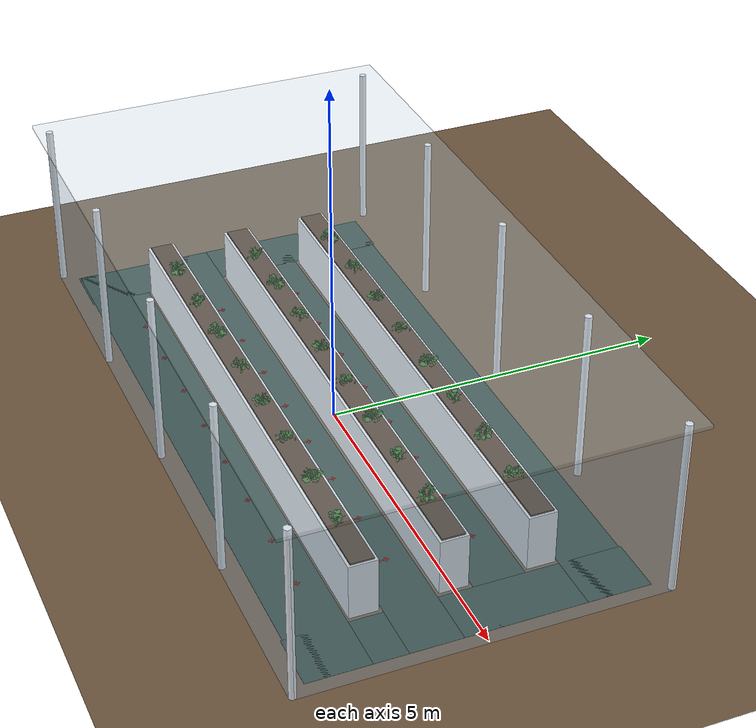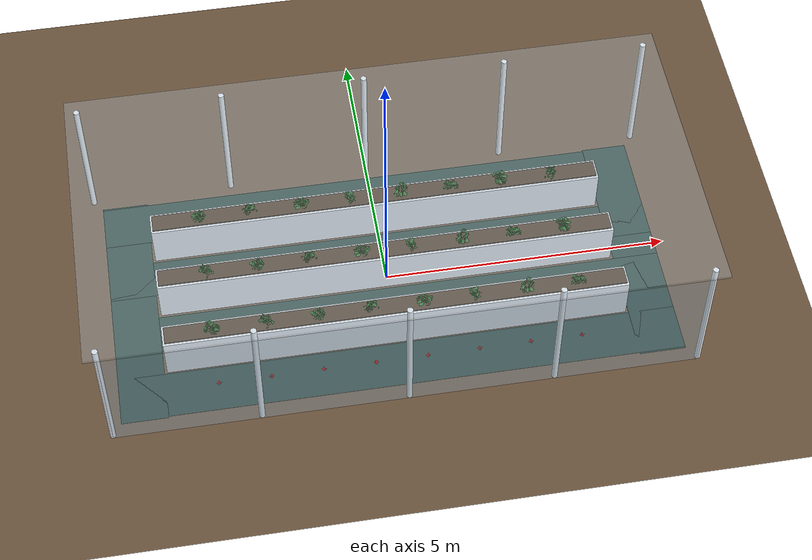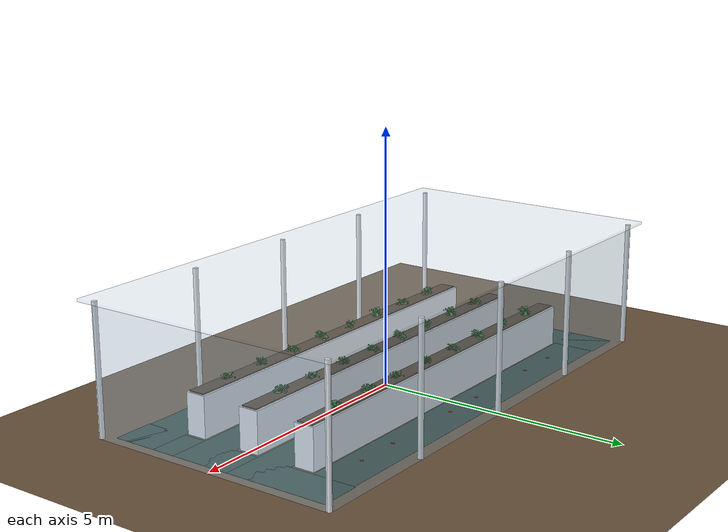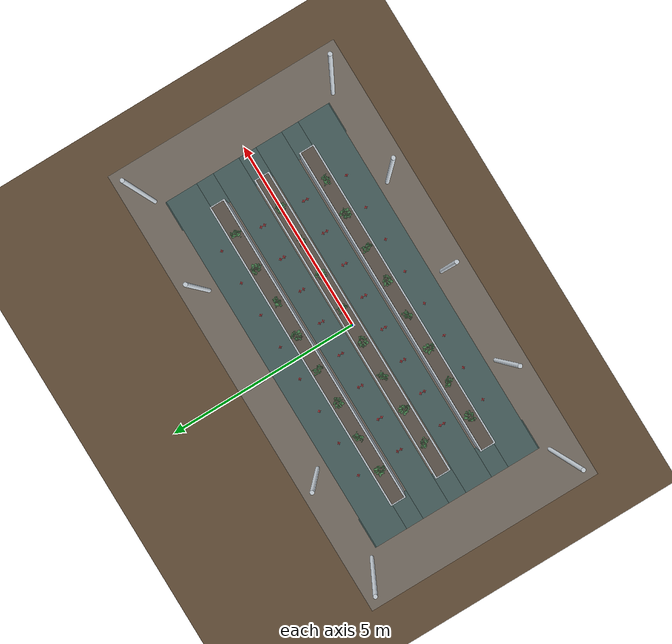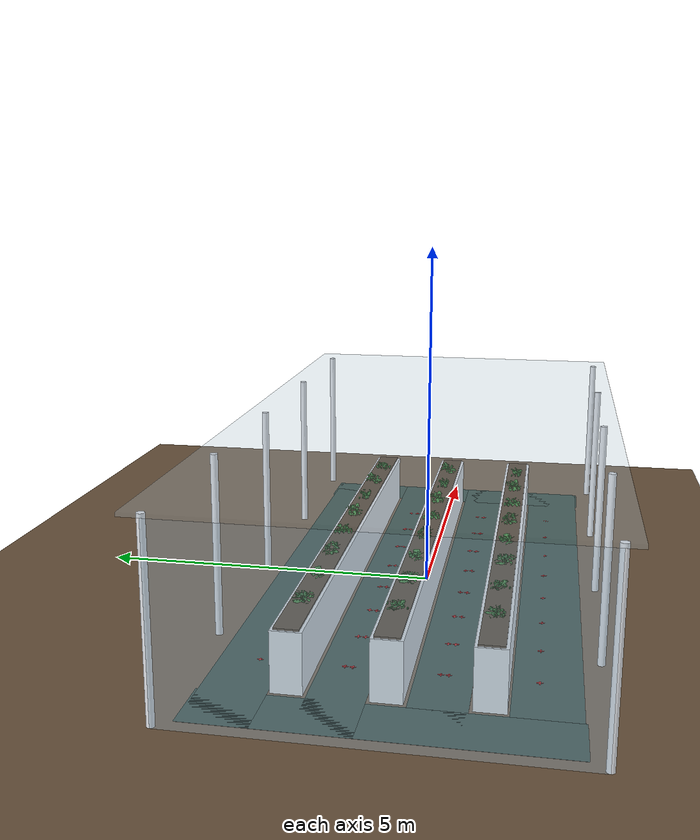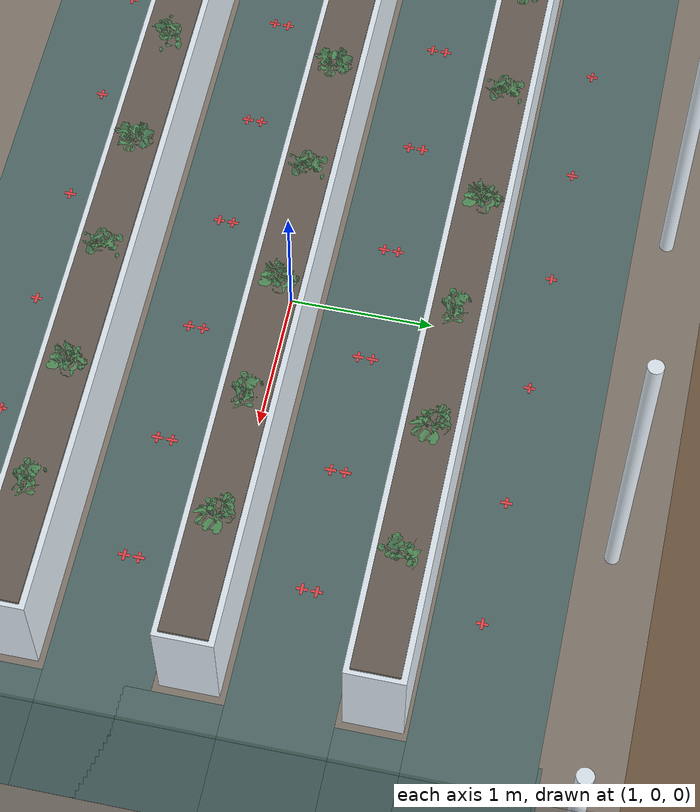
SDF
<?xml version="1.0" ?>
<!-- Generated by scripts/make_world.py (do not edit by hand).
     Strawberry greenhouse digital twin (10 x 5 m). Geometry matches sim_node.py. -->
<sdf version="1.9">
  <world name="greenhouse">
    <physics name="1ms" type="ignored">
      <max_step_size>0.004</max_step_size>
      <real_time_factor>1.0</real_time_factor>
    </physics>

    <plugin filename="gz-sim-physics-system" name="gz::sim::systems::Physics"/>
    <plugin filename="gz-sim-user-commands-system" name="gz::sim::systems::UserCommands"/>
    <plugin filename="gz-sim-scene-broadcaster-system" name="gz::sim::systems::SceneBroadcaster"/>
    <plugin filename="gz-sim-sensors-system" name="gz::sim::systems::Sensors">
      <render_engine>ogre2</render_engine>
    </plugin>

    <!-- GUI camera opens looking straight at the robot spawn (-4.6, 1.9),
         not the world origin, so the YouBot is on screen from frame one. -->
    <gui fullscreen="0">
      <plugin filename="MinimalScene" name="3D View">
        <gz-gui>
          <title>3D View</title>
          <property type="bool" key="showTitleBar">false</property>
          <property type="string" key="state">docked</property>
        </gz-gui>
        <engine>ogre2</engine>
        <scene>scene</scene>
        <ambient_light>0.6 0.6 0.6</ambient_light>
        <background_color>0.75 0.85 0.95</background_color>
        <camera_pose>-1.8 -1.4 2.6 0 0.55 2.30</camera_pose>
      </plugin>
      <plugin filename="GzSceneManager" name="Scene Manager"/>
      <plugin filename="InteractiveViewControl" name="Interactive view control"/>
      <plugin filename="CameraTracking" name="Camera Tracking"/>
      <plugin filename="WorldControl" name="World control">
        <gz-gui>
          <property type="bool" key="resizable">false</property>
          <property type="double" key="height">72</property>
          <property type="double" key="z">1</property>
          <property type="string" key="state">floating</property>
          <anchors target="3D View">
            <line own="left" target="left"/>
            <line own="bottom" target="bottom"/>
          </anchors>
        </gz-gui>
        <play_pause>true</play_pause>
        <step>true</step>
        <start_paused>false</start_paused>
      </plugin>
      <plugin filename="WorldStats" name="World stats">
        <gz-gui>
          <property type="bool" key="resizable">false</property>
          <property type="double" key="height">110</property>
          <property type="double" key="width">290</property>
          <property type="double" key="z">1</property>
          <property type="string" key="state">floating</property>
          <anchors target="3D View">
            <line own="right" target="right"/>
            <line own="bottom" target="bottom"/>
          </anchors>
        </gz-gui>
        <sim_time>true</sim_time>
        <real_time>true</real_time>
        <real_time_factor>true</real_time_factor>
      </plugin>
      <plugin filename="EntityTree" name="Entity tree"/>
    </gui>

    <scene>
      <ambient>0.55 0.55 0.52 1</ambient>
      <background>0.72 0.84 0.95 1</background>
      <grid>false</grid>
      <sky></sky>
    </scene>

    <!-- Warm late-morning sun + a soft cool fill light so the glasshouse
         interior is never flat black on the shadow side. -->
    <light type="directional" name="sun">
      <cast_shadows>true</cast_shadows>
      <pose>0 0 10 0 0 0</pose>
      <diffuse>1.0 0.96 0.86 1</diffuse>
      <specular>0.4 0.38 0.3 1</specular>
      <direction>-0.3 0.2 -0.9</direction>
    </light>
    <light type="directional" name="fill">
      <cast_shadows>false</cast_shadows>
      <pose>0 0 10 0 0 0</pose>
      <diffuse>0.28 0.30 0.34 1</diffuse>
      <specular>0 0 0 1</specular>
      <direction>0.4 -0.3 -0.8</direction>
    </light>

    <model name="ground_plane">
      <static>true</static>
      <link name="link">
        <collision name="c"><geometry><plane><normal>0 0 1</normal><size>20 20</size></plane></geometry></collision>
        <visual name="v">
          <geometry><plane><normal>0 0 1</normal><size>20 20</size></plane></geometry>
          <material><ambient>0.30 0.24 0.18 1</ambient><diffuse>0.42 0.33 0.24 1</diffuse></material>
        </visual>
      </link>
    </model>

    <model name="wall_x_pos">
      <static>true</static>
      <pose>5.0 0.0 1.250 0 0 0</pose>
      <link name="link">
        <collision name="c"><geometry><box><size>0.1 5.0 2.5</size></box></geometry></collision>
        <visual name="v">
          <geometry><box><size>0.1 5.0 2.5</size></box></geometry>
          <transparency>0.62</transparency>
          <material>
            <ambient>0.62 0.74 0.80 1</ambient>
            <diffuse>0.68 0.80 0.88 1</diffuse>
            <specular>0.9 0.9 0.9 1</specular>
          </material>
        </visual>
      </link>
    </model>
    <model name="wall_x_neg">
      <static>true</static>
      <pose>-5.0 0.0 1.250 0 0 0</pose>
      <link name="link">
        <collision name="c"><geometry><box><size>0.1 5.0 2.5</size></box></geometry></collision>
        <visual name="v">
          <geometry><box><size>0.1 5.0 2.5</size></box></geometry>
          <transparency>0.62</transparency>
          <material>
            <ambient>0.62 0.74 0.80 1</ambient>
            <diffuse>0.68 0.80 0.88 1</diffuse>
            <specular>0.9 0.9 0.9 1</specular>
          </material>
        </visual>
      </link>
    </model>
    <model name="wall_y_pos">
      <static>true</static>
      <pose>0.0 2.5 1.250 0 0 0</pose>
      <link name="link">
        <collision name="c"><geometry><box><size>10.0 0.1 2.5</size></box></geometry></collision>
        <visual name="v">
          <geometry><box><size>10.0 0.1 2.5</size></box></geometry>
          <transparency>0.62</transparency>
          <material>
            <ambient>0.62 0.74 0.80 1</ambient>
            <diffuse>0.68 0.80 0.88 1</diffuse>
            <specular>0.9 0.9 0.9 1</specular>
          </material>
        </visual>
      </link>
    </model>
    <model name="wall_y_neg">
      <static>true</static>
      <pose>0.0 -2.5 1.250 0 0 0</pose>
      <link name="link">
        <collision name="c"><geometry><box><size>10.0 0.1 2.5</size></box></geometry></collision>
        <visual name="v">
          <geometry><box><size>10.0 0.1 2.5</size></box></geometry>
          <transparency>0.62</transparency>
          <material>
            <ambient>0.62 0.74 0.80 1</ambient>
            <diffuse>0.68 0.80 0.88 1</diffuse>
            <specular>0.9 0.9 0.9 1</specular>
          </material>
        </visual>
      </link>
    </model>
    <model name="post_n0">
      <static>true</static>
      <pose>-5.0 2.5 1.250 0 0 0</pose>
      <link name="link">
        <visual name="v">
          <geometry><cylinder><radius>0.05</radius><length>2.5</length></cylinder></geometry>
          <material><ambient>0.85 0.86 0.88 1</ambient><diffuse>0.92 0.93 0.95 1</diffuse></material>
        </visual>
      </link>
    </model>
    <model name="post_s0">
      <static>true</static>
      <pose>-5.0 -2.5 1.250 0 0 0</pose>
      <link name="link">
        <visual name="v">
          <geometry><cylinder><radius>0.05</radius><length>2.5</length></cylinder></geometry>
          <material><ambient>0.85 0.86 0.88 1</ambient><diffuse>0.92 0.93 0.95 1</diffuse></material>
        </visual>
      </link>
    </model>
    <model name="post_n1">
      <static>true</static>
      <pose>-2.5 2.5 1.250 0 0 0</pose>
      <link name="link">
        <visual name="v">
          <geometry><cylinder><radius>0.05</radius><length>2.5</length></cylinder></geometry>
          <material><ambient>0.85 0.86 0.88 1</ambient><diffuse>0.92 0.93 0.95 1</diffuse></material>
        </visual>
      </link>
    </model>
    <model name="post_s1">
      <static>true</static>
      <pose>-2.5 -2.5 1.250 0 0 0</pose>
      <link name="link">
        <visual name="v">
          <geometry><cylinder><radius>0.05</radius><length>2.5</length></cylinder></geometry>
          <material><ambient>0.85 0.86 0.88 1</ambient><diffuse>0.92 0.93 0.95 1</diffuse></material>
        </visual>
      </link>
    </model>
    <model name="post_n2">
      <static>true</static>
      <pose>0.0 2.5 1.250 0 0 0</pose>
      <link name="link">
        <visual name="v">
          <geometry><cylinder><radius>0.05</radius><length>2.5</length></cylinder></geometry>
          <material><ambient>0.85 0.86 0.88 1</ambient><diffuse>0.92 0.93 0.95 1</diffuse></material>
        </visual>
      </link>
    </model>
    <model name="post_s2">
      <static>true</static>
      <pose>0.0 -2.5 1.250 0 0 0</pose>
      <link name="link">
        <visual name="v">
          <geometry><cylinder><radius>0.05</radius><length>2.5</length></cylinder></geometry>
          <material><ambient>0.85 0.86 0.88 1</ambient><diffuse>0.92 0.93 0.95 1</diffuse></material>
        </visual>
      </link>
    </model>
    <model name="post_n3">
      <static>true</static>
      <pose>2.5 2.5 1.250 0 0 0</pose>
      <link name="link">
        <visual name="v">
          <geometry><cylinder><radius>0.05</radius><length>2.5</length></cylinder></geometry>
          <material><ambient>0.85 0.86 0.88 1</ambient><diffuse>0.92 0.93 0.95 1</diffuse></material>
        </visual>
      </link>
    </model>
    <model name="post_s3">
      <static>true</static>
      <pose>2.5 -2.5 1.250 0 0 0</pose>
      <link name="link">
        <visual name="v">
          <geometry><cylinder><radius>0.05</radius><length>2.5</length></cylinder></geometry>
          <material><ambient>0.85 0.86 0.88 1</ambient><diffuse>0.92 0.93 0.95 1</diffuse></material>
        </visual>
      </link>
    </model>
    <model name="post_n4">
      <static>true</static>
      <pose>5.0 2.5 1.250 0 0 0</pose>
      <link name="link">
        <visual name="v">
          <geometry><cylinder><radius>0.05</radius><length>2.5</length></cylinder></geometry>
          <material><ambient>0.85 0.86 0.88 1</ambient><diffuse>0.92 0.93 0.95 1</diffuse></material>
        </visual>
      </link>
    </model>
    <model name="post_s4">
      <static>true</static>
      <pose>5.0 -2.5 1.250 0 0 0</pose>
      <link name="link">
        <visual name="v">
          <geometry><cylinder><radius>0.05</radius><length>2.5</length></cylinder></geometry>
          <material><ambient>0.85 0.86 0.88 1</ambient><diffuse>0.92 0.93 0.95 1</diffuse></material>
        </visual>
      </link>
    </model>
    <model name="roof">
      <static>true</static>
      <pose>0 0 2.530 0 0 0</pose>
      <link name="link">
        <visual name="v">
          <geometry><box><size>10.4 5.4 0.05</size></box></geometry>
          <transparency>0.72</transparency>
          <material>
            <ambient>0.70 0.80 0.86 1</ambient>
            <diffuse>0.75 0.85 0.92 1</diffuse>
            <specular>1 1 1 1</specular>
          </material>
        </visual>
      </link>
    </model>
    <model name="aisle_pos">
      <static>true</static>
      <pose>0 0.6 0.001 0 0 0</pose>
      <link name="link">
        <visual name="v">
          <geometry><box><size>9.70 0.72 0.002</size></box></geometry>
          <material><ambient>0.10 0.16 0.14 1</ambient><diffuse>0.15 0.25 0.21 1</diffuse></material>
        </visual>
      </link>
    </model>
    <model name="aisle_neg">
      <static>true</static>
      <pose>0 -0.6 0.001 0 0 0</pose>
      <link name="link">
        <visual name="v">
          <geometry><box><size>9.70 0.72 0.002</size></box></geometry>
          <material><ambient>0.10 0.16 0.14 1</ambient><diffuse>0.15 0.25 0.21 1</diffuse></material>
        </visual>
      </link>
    </model>
    <model name="aisle_far_pos">
      <static>true</static>
      <pose>0 1.85 0.001 0 0 0</pose>
      <link name="link">
        <visual name="v">
          <geometry><box><size>9.70 0.85 0.002</size></box></geometry>
          <material><ambient>0.10 0.16 0.14 1</ambient><diffuse>0.15 0.25 0.21 1</diffuse></material>
        </visual>
      </link>
    </model>
    <model name="aisle_far_neg">
      <static>true</static>
      <pose>0 -1.85 0.001 0 0 0</pose>
      <link name="link">
        <visual name="v">
          <geometry><box><size>9.70 0.85 0.002</size></box></geometry>
          <material><ambient>0.10 0.16 0.14 1</ambient><diffuse>0.15 0.25 0.21 1</diffuse></material>
        </visual>
      </link>
    </model>
    <model name="lane_east">
      <static>true</static>
      <pose>4.45 0 0.001 0 0 0</pose>
      <link name="link">
        <visual name="v">
          <geometry><box><size>0.80 4.60 0.002</size></box></geometry>
          <material><ambient>0.10 0.16 0.14 1</ambient><diffuse>0.15 0.25 0.21 1</diffuse></material>
        </visual>
      </link>
    </model>
    <model name="lane_west">
      <static>true</static>
      <pose>-4.45 0 0.001 0 0 0</pose>
      <link name="link">
        <visual name="v">
          <geometry><box><size>0.80 4.60 0.002</size></box></geometry>
          <material><ambient>0.10 0.16 0.14 1</ambient><diffuse>0.15 0.25 0.21 1</diffuse></material>
        </visual>
      </link>
    </model>
    <model name="gutter_0">
      <static>true</static>
      <pose>0 -1.2 0 0 0 0</pose>
      <link name="link">
        <pose>0 0 0.400 0 0 0</pose>
        <collision name="c"><geometry><box><size>8.0 0.4 0.8</size></box></geometry></collision>
        <visual name="body">
          <geometry><box><size>8.0 0.4 0.8</size></box></geometry>
          <material>
            <ambient>0.80 0.81 0.83 1</ambient>
            <diffuse>0.92 0.93 0.95 1</diffuse>
            <specular>0.3 0.3 0.3 1</specular>
          </material>
        </visual>
        <visual name="soil">
          <pose>0 0 0.411 0 0 0</pose>
          <geometry><box><size>7.94 0.32 0.025</size></box></geometry>
          <material><ambient>0.20 0.13 0.08 1</ambient><diffuse>0.28 0.19 0.11 1</diffuse></material>
        </visual>
      </link>
    </model>
    <model name="plant_0_0">
      <static>true</static>
      <pose>-3.15 -1.2 0 0 0 0</pose>
      <link name="link">
        <visual name="plant">
          <pose>0 0 0.8877 0 0 1.2741</pose>
          <geometry>
            <mesh>
              <uri>file:///workspace/ros2_stage/cloud_agri/meshes/strawberry_b.stl</uri>
              <scale>0.16036 0.16036 0.16036</scale>
            </mesh>
          </geometry>
          <material><ambient>0.06 0.20 0.05 1</ambient><diffuse>0.16 0.44 0.13 1</diffuse><specular>0.10 0.16 0.08 1</specular></material>
        </visual>
        <collision name="stem">
          <pose>0 0 0.910 0 0 0</pose>
          <geometry><cylinder><radius>0.11</radius><length>0.22</length></cylinder></geometry>
        </collision>
      </link>
    </model>
    <model name="plant_0_1">
      <static>true</static>
      <pose>-2.25 -1.2 0 0 0 0</pose>
      <link name="link">
        <visual name="plant">
          <pose>0 0 0.8758 0 0 1.9199</pose>
          <geometry>
            <mesh>
              <uri>file:///workspace/ros2_stage/cloud_agri/meshes/strawberry_a.stl</uri>
              <scale>0.15180 0.15180 0.15180</scale>
            </mesh>
          </geometry>
          <material><ambient>0.06 0.20 0.05 1</ambient><diffuse>0.16 0.44 0.13 1</diffuse><specular>0.10 0.16 0.08 1</specular></material>
        </visual>
        <collision name="stem">
          <pose>0 0 0.910 0 0 0</pose>
          <geometry><cylinder><radius>0.11</radius><length>0.22</length></cylinder></geometry>
        </collision>
      </link>
    </model>
    <model name="plant_0_2">
      <static>true</static>
      <pose>-1.3499999999999999 -1.2 0 0 0 0</pose>
      <link name="link">
        <visual name="plant">
          <pose>0 0 0.8877 0 0 2.5656</pose>
          <geometry>
            <mesh>
              <uri>file:///workspace/ros2_stage/cloud_agri/meshes/strawberry_b.stl</uri>
              <scale>0.16036 0.16036 0.16036</scale>
            </mesh>
          </geometry>
          <material><ambient>0.06 0.20 0.05 1</ambient><diffuse>0.16 0.44 0.13 1</diffuse><specular>0.10 0.16 0.08 1</specular></material>
        </visual>
        <collision name="stem">
          <pose>0 0 0.910 0 0 0</pose>
          <geometry><cylinder><radius>0.11</radius><length>0.22</length></cylinder></geometry>
        </collision>
      </link>
    </model>
    <model name="plant_0_3">
      <static>true</static>
      <pose>-0.44999999999999973 -1.2 0 0 0 0</pose>
      <link name="link">
        <visual name="plant">
          <pose>0 0 0.8758 0 0 3.2114</pose>
          <geometry>
            <mesh>
              <uri>file:///workspace/ros2_stage/cloud_agri/meshes/strawberry_a.stl</uri>
              <scale>0.15180 0.15180 0.15180</scale>
            </mesh>
          </geometry>
          <material><ambient>0.06 0.20 0.05 1</ambient><diffuse>0.16 0.44 0.13 1</diffuse><specular>0.10 0.16 0.08 1</specular></material>
        </visual>
        <collision name="stem">
          <pose>0 0 0.910 0 0 0</pose>
          <geometry><cylinder><radius>0.11</radius><length>0.22</length></cylinder></geometry>
        </collision>
      </link>
    </model>
    <model name="plant_0_4">
      <static>true</static>
      <pose>0.4500000000000002 -1.2 0 0 0 0</pose>
      <link name="link">
        <visual name="plant">
          <pose>0 0 0.8877 0 0 3.8572</pose>
          <geometry>
            <mesh>
              <uri>file:///workspace/ros2_stage/cloud_agri/meshes/strawberry_b.stl</uri>
              <scale>0.16036 0.16036 0.16036</scale>
            </mesh>
          </geometry>
          <material><ambient>0.06 0.20 0.05 1</ambient><diffuse>0.16 0.44 0.13 1</diffuse><specular>0.10 0.16 0.08 1</specular></material>
        </visual>
        <collision name="stem">
          <pose>0 0 0.910 0 0 0</pose>
          <geometry><cylinder><radius>0.11</radius><length>0.22</length></cylinder></geometry>
        </collision>
      </link>
    </model>
    <model name="plant_0_5">
      <static>true</static>
      <pose>1.35 -1.2 0 0 0 0</pose>
      <link name="link">
        <visual name="plant">
          <pose>0 0 0.8758 0 0 4.5029</pose>
          <geometry>
            <mesh>
              <uri>file:///workspace/ros2_stage/cloud_agri/meshes/strawberry_a.stl</uri>
              <scale>0.15180 0.15180 0.15180</scale>
            </mesh>
          </geometry>
          <material><ambient>0.06 0.20 0.05 1</ambient><diffuse>0.16 0.44 0.13 1</diffuse><specular>0.10 0.16 0.08 1</specular></material>
        </visual>
        <collision name="stem">
          <pose>0 0 0.910 0 0 0</pose>
          <geometry><cylinder><radius>0.11</radius><length>0.22</length></cylinder></geometry>
        </collision>
      </link>
    </model>
    <model name="plant_0_6">
      <static>true</static>
      <pose>2.2500000000000004 -1.2 0 0 0 0</pose>
      <link name="link">
        <visual name="plant">
          <pose>0 0 0.8877 0 0 5.1487</pose>
          <geometry>
            <mesh>
              <uri>file:///workspace/ros2_stage/cloud_agri/meshes/strawberry_b.stl</uri>
              <scale>0.16036 0.16036 0.16036</scale>
            </mesh>
          </geometry>
          <material><ambient>0.06 0.20 0.05 1</ambient><diffuse>0.16 0.44 0.13 1</diffuse><specular>0.10 0.16 0.08 1</specular></material>
        </visual>
        <collision name="stem">
          <pose>0 0 0.910 0 0 0</pose>
          <geometry><cylinder><radius>0.11</radius><length>0.22</length></cylinder></geometry>
        </collision>
      </link>
    </model>
    <model name="plant_0_7">
      <static>true</static>
      <pose>3.15 -1.2 0 0 0 0</pose>
      <link name="link">
        <visual name="plant">
          <pose>0 0 0.8758 0 0 5.7945</pose>
          <geometry>
            <mesh>
              <uri>file:///workspace/ros2_stage/cloud_agri/meshes/strawberry_a.stl</uri>
              <scale>0.15180 0.15180 0.15180</scale>
            </mesh>
          </geometry>
          <material><ambient>0.06 0.20 0.05 1</ambient><diffuse>0.16 0.44 0.13 1</diffuse><specular>0.10 0.16 0.08 1</specular></material>
        </visual>
        <collision name="stem">
          <pose>0 0 0.910 0 0 0</pose>
          <geometry><cylinder><radius>0.11</radius><length>0.22</length></cylinder></geometry>
        </collision>
      </link>
    </model>
    <model name="gutter_1">
      <static>true</static>
      <pose>0 0.0 0 0 0 0</pose>
      <link name="link">
        <pose>0 0 0.400 0 0 0</pose>
        <collision name="c"><geometry><box><size>8.0 0.4 0.8</size></box></geometry></collision>
        <visual name="body">
          <geometry><box><size>8.0 0.4 0.8</size></box></geometry>
          <material>
            <ambient>0.80 0.81 0.83 1</ambient>
            <diffuse>0.92 0.93 0.95 1</diffuse>
            <specular>0.3 0.3 0.3 1</specular>
          </material>
        </visual>
        <visual name="soil">
          <pose>0 0 0.411 0 0 0</pose>
          <geometry><box><size>7.94 0.32 0.025</size></box></geometry>
          <material><ambient>0.20 0.13 0.08 1</ambient><diffuse>0.28 0.19 0.11 1</diffuse></material>
        </visual>
      </link>
    </model>
    <model name="plant_1_0">
      <static>true</static>
      <pose>-3.15 0.0 0 0 0 0</pose>
      <link name="link">
        <visual name="plant">
          <pose>0 0 0.8758 0 0 1.9199</pose>
          <geometry>
            <mesh>
              <uri>file:///workspace/ros2_stage/cloud_agri/meshes/strawberry_a.stl</uri>
              <scale>0.15180 0.15180 0.15180</scale>
            </mesh>
          </geometry>
          <material><ambient>0.06 0.20 0.05 1</ambient><diffuse>0.16 0.44 0.13 1</diffuse><specular>0.10 0.16 0.08 1</specular></material>
        </visual>
        <collision name="stem">
          <pose>0 0 0.910 0 0 0</pose>
          <geometry><cylinder><radius>0.11</radius><length>0.22</length></cylinder></geometry>
        </collision>
      </link>
    </model>
    <model name="plant_1_1">
      <static>true</static>
      <pose>-2.25 0.0 0 0 0 0</pose>
      <link name="link">
        <visual name="plant">
          <pose>0 0 0.8877 0 0 2.5656</pose>
          <geometry>
            <mesh>
              <uri>file:///workspace/ros2_stage/cloud_agri/meshes/strawberry_b.stl</uri>
              <scale>0.16036 0.16036 0.16036</scale>
            </mesh>
          </geometry>
          <material><ambient>0.06 0.20 0.05 1</ambient><diffuse>0.16 0.44 0.13 1</diffuse><specular>0.10 0.16 0.08 1</specular></material>
        </visual>
        <collision name="stem">
          <pose>0 0 0.910 0 0 0</pose>
          <geometry><cylinder><radius>0.11</radius><length>0.22</length></cylinder></geometry>
        </collision>
      </link>
    </model>
    <model name="plant_1_2">
      <static>true</static>
      <pose>-1.3499999999999999 0.0 0 0 0 0</pose>
      <link name="link">
        <visual name="plant">
          <pose>0 0 0.8758 0 0 3.2114</pose>
          <geometry>
            <mesh>
              <uri>file:///workspace/ros2_stage/cloud_agri/meshes/strawberry_a.stl</uri>
              <scale>0.15180 0.15180 0.15180</scale>
            </mesh>
          </geometry>
          <material><ambient>0.06 0.20 0.05 1</ambient><diffuse>0.16 0.44 0.13 1</diffuse><specular>0.10 0.16 0.08 1</specular></material>
        </visual>
        <collision name="stem">
          <pose>0 0 0.910 0 0 0</pose>
          <geometry><cylinder><radius>0.11</radius><length>0.22</length></cylinder></geometry>
        </collision>
      </link>
    </model>
    <model name="plant_1_3">
      <static>true</static>
      <pose>-0.44999999999999973 0.0 0 0 0 0</pose>
      <link name="link">
        <visual name="plant">
          <pose>0 0 0.8877 0 0 3.8572</pose>
          <geometry>
            <mesh>
              <uri>file:///workspace/ros2_stage/cloud_agri/meshes/strawberry_b.stl</uri>
              <scale>0.16036 0.16036 0.16036</scale>
            </mesh>
          </geometry>
          <material><ambient>0.06 0.20 0.05 1</ambient><diffuse>0.16 0.44 0.13 1</diffuse><specular>0.10 0.16 0.08 1</specular></material>
        </visual>
        <collision name="stem">
          <pose>0 0 0.910 0 0 0</pose>
          <geometry><cylinder><radius>0.11</radius><length>0.22</length></cylinder></geometry>
        </collision>
      </link>
    </model>
    <model name="plant_1_4">
      <static>true</static>
      <pose>0.4500000000000002 0.0 0 0 0 0</pose>
      <link name="link">
        <visual name="plant">
          <pose>0 0 0.8758 0 0 4.5029</pose>
          <geometry>
            <mesh>
              <uri>file:///workspace/ros2_stage/cloud_agri/meshes/strawberry_a.stl</uri>
              <scale>0.15180 0.15180 0.15180</scale>
            </mesh>
          </geometry>
          <material><ambient>0.06 0.20 0.05 1</ambient><diffuse>0.16 0.44 0.13 1</diffuse><specular>0.10 0.16 0.08 1</specular></material>
        </visual>
        <collision name="stem">
          <pose>0 0 0.910 0 0 0</pose>
          <geometry><cylinder><radius>0.11</radius><length>0.22</length></cylinder></geometry>
        </collision>
      </link>
    </model>
    <model name="plant_1_5">
      <static>true</static>
      <pose>1.35 0.0 0 0 0 0</pose>
      <link name="link">
        <visual name="plant">
          <pose>0 0 0.8877 0 0 5.1487</pose>
          <geometry>
            <mesh>
              <uri>file:///workspace/ros2_stage/cloud_agri/meshes/strawberry_b.stl</uri>
              <scale>0.16036 0.16036 0.16036</scale>
            </mesh>
          </geometry>
          <material><ambient>0.06 0.20 0.05 1</ambient><diffuse>0.16 0.44 0.13 1</diffuse><specular>0.10 0.16 0.08 1</specular></material>
        </visual>
        <collision name="stem">
          <pose>0 0 0.910 0 0 0</pose>
          <geometry><cylinder><radius>0.11</radius><length>0.22</length></cylinder></geometry>
        </collision>
      </link>
    </model>
    <model name="plant_1_6">
      <static>true</static>
      <pose>2.2500000000000004 0.0 0 0 0 0</pose>
      <link name="link">
        <visual name="plant">
          <pose>0 0 0.8758 0 0 5.7945</pose>
          <geometry>
            <mesh>
              <uri>file:///workspace/ros2_stage/cloud_agri/meshes/strawberry_a.stl</uri>
              <scale>0.15180 0.15180 0.15180</scale>
            </mesh>
          </geometry>
          <material><ambient>0.06 0.20 0.05 1</ambient><diffuse>0.16 0.44 0.13 1</diffuse><specular>0.10 0.16 0.08 1</specular></material>
        </visual>
        <collision name="stem">
          <pose>0 0 0.910 0 0 0</pose>
          <geometry><cylinder><radius>0.11</radius><length>0.22</length></cylinder></geometry>
        </collision>
      </link>
    </model>
    <model name="plant_1_7">
      <static>true</static>
      <pose>3.15 0.0 0 0 0 0</pose>
      <link name="link">
        <visual name="plant">
          <pose>0 0 0.8877 0 0 0.1571</pose>
          <geometry>
            <mesh>
              <uri>file:///workspace/ros2_stage/cloud_agri/meshes/strawberry_b.stl</uri>
              <scale>0.16036 0.16036 0.16036</scale>
            </mesh>
          </geometry>
          <material><ambient>0.06 0.20 0.05 1</ambient><diffuse>0.16 0.44 0.13 1</diffuse><specular>0.10 0.16 0.08 1</specular></material>
        </visual>
        <collision name="stem">
          <pose>0 0 0.910 0 0 0</pose>
          <geometry><cylinder><radius>0.11</radius><length>0.22</length></cylinder></geometry>
        </collision>
      </link>
    </model>
    <model name="gutter_2">
      <static>true</static>
      <pose>0 1.2 0 0 0 0</pose>
      <link name="link">
        <pose>0 0 0.400 0 0 0</pose>
        <collision name="c"><geometry><box><size>8.0 0.4 0.8</size></box></geometry></collision>
        <visual name="body">
          <geometry><box><size>8.0 0.4 0.8</size></box></geometry>
          <material>
            <ambient>0.80 0.81 0.83 1</ambient>
            <diffuse>0.92 0.93 0.95 1</diffuse>
            <specular>0.3 0.3 0.3 1</specular>
          </material>
        </visual>
        <visual name="soil">
          <pose>0 0 0.411 0 0 0</pose>
          <geometry><box><size>7.94 0.32 0.025</size></box></geometry>
          <material><ambient>0.20 0.13 0.08 1</ambient><diffuse>0.28 0.19 0.11 1</diffuse></material>
        </visual>
      </link>
    </model>
    <model name="plant_2_0">
      <static>true</static>
      <pose>-3.15 1.2 0 0 0 0</pose>
      <link name="link">
        <visual name="plant">
          <pose>0 0 0.8877 0 0 2.5656</pose>
          <geometry>
            <mesh>
              <uri>file:///workspace/ros2_stage/cloud_agri/meshes/strawberry_b.stl</uri>
              <scale>0.16036 0.16036 0.16036</scale>
            </mesh>
          </geometry>
          <material><ambient>0.06 0.20 0.05 1</ambient><diffuse>0.16 0.44 0.13 1</diffuse><specular>0.10 0.16 0.08 1</specular></material>
        </visual>
        <collision name="stem">
          <pose>0 0 0.910 0 0 0</pose>
          <geometry><cylinder><radius>0.11</radius><length>0.22</length></cylinder></geometry>
        </collision>
      </link>
    </model>
    <model name="plant_2_1">
      <static>true</static>
      <pose>-2.25 1.2 0 0 0 0</pose>
      <link name="link">
        <visual name="plant">
          <pose>0 0 0.8758 0 0 3.2114</pose>
          <geometry>
            <mesh>
              <uri>file:///workspace/ros2_stage/cloud_agri/meshes/strawberry_a.stl</uri>
              <scale>0.15180 0.15180 0.15180</scale>
            </mesh>
          </geometry>
          <material><ambient>0.06 0.20 0.05 1</ambient><diffuse>0.16 0.44 0.13 1</diffuse><specular>0.10 0.16 0.08 1</specular></material>
        </visual>
        <collision name="stem">
          <pose>0 0 0.910 0 0 0</pose>
          <geometry><cylinder><radius>0.11</radius><length>0.22</length></cylinder></geometry>
        </collision>
      </link>
    </model>
    <model name="plant_2_2">
      <static>true</static>
      <pose>-1.3499999999999999 1.2 0 0 0 0</pose>
      <link name="link">
        <visual name="plant">
          <pose>0 0 0.8877 0 0 3.8572</pose>
          <geometry>
            <mesh>
              <uri>file:///workspace/ros2_stage/cloud_agri/meshes/strawberry_b.stl</uri>
              <scale>0.16036 0.16036 0.16036</scale>
            </mesh>
          </geometry>
          <material><ambient>0.06 0.20 0.05 1</ambient><diffuse>0.16 0.44 0.13 1</diffuse><specular>0.10 0.16 0.08 1</specular></material>
        </visual>
        <collision name="stem">
          <pose>0 0 0.910 0 0 0</pose>
          <geometry><cylinder><radius>0.11</radius><length>0.22</length></cylinder></geometry>
        </collision>
      </link>
    </model>
    <model name="plant_2_3">
      <static>true</static>
      <pose>-0.44999999999999973 1.2 0 0 0 0</pose>
      <link name="link">
        <visual name="plant">
          <pose>0 0 0.8758 0 0 4.5029</pose>
          <geometry>
            <mesh>
              <uri>file:///workspace/ros2_stage/cloud_agri/meshes/strawberry_a.stl</uri>
              <scale>0.15180 0.15180 0.15180</scale>
            </mesh>
          </geometry>
          <material><ambient>0.06 0.20 0.05 1</ambient><diffuse>0.16 0.44 0.13 1</diffuse><specular>0.10 0.16 0.08 1</specular></material>
        </visual>
        <collision name="stem">
          <pose>0 0 0.910 0 0 0</pose>
          <geometry><cylinder><radius>0.11</radius><length>0.22</length></cylinder></geometry>
        </collision>
      </link>
    </model>
    <model name="plant_2_4">
      <static>true</static>
      <pose>0.4500000000000002 1.2 0 0 0 0</pose>
      <link name="link">
        <visual name="plant">
          <pose>0 0 0.8877 0 0 5.1487</pose>
          <geometry>
            <mesh>
              <uri>file:///workspace/ros2_stage/cloud_agri/meshes/strawberry_b.stl</uri>
              <scale>0.16036 0.16036 0.16036</scale>
            </mesh>
          </geometry>
          <material><ambient>0.06 0.20 0.05 1</ambient><diffuse>0.16 0.44 0.13 1</diffuse><specular>0.10 0.16 0.08 1</specular></material>
        </visual>
        <collision name="stem">
          <pose>0 0 0.910 0 0 0</pose>
          <geometry><cylinder><radius>0.11</radius><length>0.22</length></cylinder></geometry>
        </collision>
      </link>
    </model>
    <model name="plant_2_5">
      <static>true</static>
      <pose>1.35 1.2 0 0 0 0</pose>
      <link name="link">
        <visual name="plant">
          <pose>0 0 0.8758 0 0 5.7945</pose>
          <geometry>
            <mesh>
              <uri>file:///workspace/ros2_stage/cloud_agri/meshes/strawberry_a.stl</uri>
              <scale>0.15180 0.15180 0.15180</scale>
            </mesh>
          </geometry>
          <material><ambient>0.06 0.20 0.05 1</ambient><diffuse>0.16 0.44 0.13 1</diffuse><specular>0.10 0.16 0.08 1</specular></material>
        </visual>
        <collision name="stem">
          <pose>0 0 0.910 0 0 0</pose>
          <geometry><cylinder><radius>0.11</radius><length>0.22</length></cylinder></geometry>
        </collision>
      </link>
    </model>
    <model name="plant_2_6">
      <static>true</static>
      <pose>2.2500000000000004 1.2 0 0 0 0</pose>
      <link name="link">
        <visual name="plant">
          <pose>0 0 0.8877 0 0 0.1571</pose>
          <geometry>
            <mesh>
              <uri>file:///workspace/ros2_stage/cloud_agri/meshes/strawberry_b.stl</uri>
              <scale>0.16036 0.16036 0.16036</scale>
            </mesh>
          </geometry>
          <material><ambient>0.06 0.20 0.05 1</ambient><diffuse>0.16 0.44 0.13 1</diffuse><specular>0.10 0.16 0.08 1</specular></material>
        </visual>
        <collision name="stem">
          <pose>0 0 0.910 0 0 0</pose>
          <geometry><cylinder><radius>0.11</radius><length>0.22</length></cylinder></geometry>
        </collision>
      </link>
    </model>
    <model name="plant_2_7">
      <static>true</static>
      <pose>3.15 1.2 0 0 0 0</pose>
      <link name="link">
        <visual name="plant">
          <pose>0 0 0.8758 0 0 0.8029</pose>
          <geometry>
            <mesh>
              <uri>file:///workspace/ros2_stage/cloud_agri/meshes/strawberry_a.stl</uri>
              <scale>0.15180 0.15180 0.15180</scale>
            </mesh>
          </geometry>
          <material><ambient>0.06 0.20 0.05 1</ambient><diffuse>0.16 0.44 0.13 1</diffuse><specular>0.10 0.16 0.08 1</specular></material>
        </visual>
        <collision name="stem">
          <pose>0 0 0.910 0 0 0</pose>
          <geometry><cylinder><radius>0.11</radius><length>0.22</length></cylinder></geometry>
        </collision>
      </link>
    </model>

    <!-- station P1,1R -->
    <model name="cross_P1_1R">
      <static>true</static>
      <pose>-3.1500 -1.7500 0.004 0 0 0</pose>
      <link name="link">
      <visual name="x">
          <geometry><box><size>0.0800 0.0200 0.002</size></box></geometry>
        <material>
            <ambient>0.85 0.05 0.05 1</ambient>
            <diffuse>0.95 0.06 0.06 1</diffuse>
            <specular>0.2 0.02 0.02 1</specular>
            <emissive>0.45 0.02 0.02 1</emissive>
          </material>
        </visual>
      <visual name="y">
          <geometry><box><size>0.0200 0.0800 0.002</size></box></geometry>
        <material>
            <ambient>0.85 0.05 0.05 1</ambient>
            <diffuse>0.95 0.06 0.06 1</diffuse>
            <specular>0.2 0.02 0.02 1</specular>
            <emissive>0.45 0.02 0.02 1</emissive>
          </material>
        </visual>
      </link>
    </model>
    <!-- station P1,1L -->
    <model name="cross_P1_1L">
      <static>true</static>
      <pose>-3.1500 -0.6500 0.004 0 0 0</pose>
      <link name="link">
      <visual name="x">
          <geometry><box><size>0.0800 0.0200 0.002</size></box></geometry>
        <material>
            <ambient>0.85 0.05 0.05 1</ambient>
            <diffuse>0.95 0.06 0.06 1</diffuse>
            <specular>0.2 0.02 0.02 1</specular>
            <emissive>0.45 0.02 0.02 1</emissive>
          </material>
        </visual>
      <visual name="y">
          <geometry><box><size>0.0200 0.0800 0.002</size></box></geometry>
        <material>
            <ambient>0.85 0.05 0.05 1</ambient>
            <diffuse>0.95 0.06 0.06 1</diffuse>
            <specular>0.2 0.02 0.02 1</specular>
            <emissive>0.45 0.02 0.02 1</emissive>
          </material>
        </visual>
      </link>
    </model>
    <!-- station P1,2R -->
    <model name="cross_P1_2R">
      <static>true</static>
      <pose>-2.2500 -1.7500 0.004 0 0 0</pose>
      <link name="link">
      <visual name="x">
          <geometry><box><size>0.0800 0.0200 0.002</size></box></geometry>
        <material>
            <ambient>0.85 0.05 0.05 1</ambient>
            <diffuse>0.95 0.06 0.06 1</diffuse>
            <specular>0.2 0.02 0.02 1</specular>
            <emissive>0.45 0.02 0.02 1</emissive>
          </material>
        </visual>
      <visual name="y">
          <geometry><box><size>0.0200 0.0800 0.002</size></box></geometry>
        <material>
            <ambient>0.85 0.05 0.05 1</ambient>
            <diffuse>0.95 0.06 0.06 1</diffuse>
            <specular>0.2 0.02 0.02 1</specular>
            <emissive>0.45 0.02 0.02 1</emissive>
          </material>
        </visual>
      </link>
    </model>
    <!-- station P1,2L -->
    <model name="cross_P1_2L">
      <static>true</static>
      <pose>-2.2500 -0.6500 0.004 0 0 0</pose>
      <link name="link">
      <visual name="x">
          <geometry><box><size>0.0800 0.0200 0.002</size></box></geometry>
        <material>
            <ambient>0.85 0.05 0.05 1</ambient>
            <diffuse>0.95 0.06 0.06 1</diffuse>
            <specular>0.2 0.02 0.02 1</specular>
            <emissive>0.45 0.02 0.02 1</emissive>
          </material>
        </visual>
      <visual name="y">
          <geometry><box><size>0.0200 0.0800 0.002</size></box></geometry>
        <material>
            <ambient>0.85 0.05 0.05 1</ambient>
            <diffuse>0.95 0.06 0.06 1</diffuse>
            <specular>0.2 0.02 0.02 1</specular>
            <emissive>0.45 0.02 0.02 1</emissive>
          </material>
        </visual>
      </link>
    </model>
    <!-- station P1,3R -->
    <model name="cross_P1_3R">
      <static>true</static>
      <pose>-1.3500 -1.7500 0.004 0 0 0</pose>
      <link name="link">
      <visual name="x">
          <geometry><box><size>0.0800 0.0200 0.002</size></box></geometry>
        <material>
            <ambient>0.85 0.05 0.05 1</ambient>
            <diffuse>0.95 0.06 0.06 1</diffuse>
            <specular>0.2 0.02 0.02 1</specular>
            <emissive>0.45 0.02 0.02 1</emissive>
          </material>
        </visual>
      <visual name="y">
          <geometry><box><size>0.0200 0.0800 0.002</size></box></geometry>
        <material>
            <ambient>0.85 0.05 0.05 1</ambient>
            <diffuse>0.95 0.06 0.06 1</diffuse>
            <specular>0.2 0.02 0.02 1</specular>
            <emissive>0.45 0.02 0.02 1</emissive>
          </material>
        </visual>
      </link>
    </model>
    <!-- station P1,3L -->
    <model name="cross_P1_3L">
      <static>true</static>
      <pose>-1.3500 -0.6500 0.004 0 0 0</pose>
      <link name="link">
      <visual name="x">
          <geometry><box><size>0.0800 0.0200 0.002</size></box></geometry>
        <material>
            <ambient>0.85 0.05 0.05 1</ambient>
            <diffuse>0.95 0.06 0.06 1</diffuse>
            <specular>0.2 0.02 0.02 1</specular>
            <emissive>0.45 0.02 0.02 1</emissive>
          </material>
        </visual>
      <visual name="y">
          <geometry><box><size>0.0200 0.0800 0.002</size></box></geometry>
        <material>
            <ambient>0.85 0.05 0.05 1</ambient>
            <diffuse>0.95 0.06 0.06 1</diffuse>
            <specular>0.2 0.02 0.02 1</specular>
            <emissive>0.45 0.02 0.02 1</emissive>
          </material>
        </visual>
      </link>
    </model>
    <!-- station P1,4R -->
    <model name="cross_P1_4R">
      <static>true</static>
      <pose>-0.4500 -1.7500 0.004 0 0 0</pose>
      <link name="link">
      <visual name="x">
          <geometry><box><size>0.0800 0.0200 0.002</size></box></geometry>
        <material>
            <ambient>0.85 0.05 0.05 1</ambient>
            <diffuse>0.95 0.06 0.06 1</diffuse>
            <specular>0.2 0.02 0.02 1</specular>
            <emissive>0.45 0.02 0.02 1</emissive>
          </material>
        </visual>
      <visual name="y">
          <geometry><box><size>0.0200 0.0800 0.002</size></box></geometry>
        <material>
            <ambient>0.85 0.05 0.05 1</ambient>
            <diffuse>0.95 0.06 0.06 1</diffuse>
            <specular>0.2 0.02 0.02 1</specular>
            <emissive>0.45 0.02 0.02 1</emissive>
          </material>
        </visual>
      </link>
    </model>
    <!-- station P1,4L -->
    <model name="cross_P1_4L">
      <static>true</static>
      <pose>-0.4500 -0.6500 0.004 0 0 0</pose>
      <link name="link">
      <visual name="x">
          <geometry><box><size>0.0800 0.0200 0.002</size></box></geometry>
        <material>
            <ambient>0.85 0.05 0.05 1</ambient>
            <diffuse>0.95 0.06 0.06 1</diffuse>
            <specular>0.2 0.02 0.02 1</specular>
            <emissive>0.45 0.02 0.02 1</emissive>
          </material>
        </visual>
      <visual name="y">
          <geometry><box><size>0.0200 0.0800 0.002</size></box></geometry>
        <material>
            <ambient>0.85 0.05 0.05 1</ambient>
            <diffuse>0.95 0.06 0.06 1</diffuse>
            <specular>0.2 0.02 0.02 1</specular>
            <emissive>0.45 0.02 0.02 1</emissive>
          </material>
        </visual>
      </link>
    </model>
    <!-- station P1,5R -->
    <model name="cross_P1_5R">
      <static>true</static>
      <pose>0.4500 -1.7500 0.004 0 0 0</pose>
      <link name="link">
      <visual name="x">
          <geometry><box><size>0.0800 0.0200 0.002</size></box></geometry>
        <material>
            <ambient>0.85 0.05 0.05 1</ambient>
            <diffuse>0.95 0.06 0.06 1</diffuse>
            <specular>0.2 0.02 0.02 1</specular>
            <emissive>0.45 0.02 0.02 1</emissive>
          </material>
        </visual>
      <visual name="y">
          <geometry><box><size>0.0200 0.0800 0.002</size></box></geometry>
        <material>
            <ambient>0.85 0.05 0.05 1</ambient>
            <diffuse>0.95 0.06 0.06 1</diffuse>
            <specular>0.2 0.02 0.02 1</specular>
            <emissive>0.45 0.02 0.02 1</emissive>
          </material>
        </visual>
      </link>
    </model>
    <!-- station P1,5L -->
    <model name="cross_P1_5L">
      <static>true</static>
      <pose>0.4500 -0.6500 0.004 0 0 0</pose>
      <link name="link">
      <visual name="x">
          <geometry><box><size>0.0800 0.0200 0.002</size></box></geometry>
        <material>
            <ambient>0.85 0.05 0.05 1</ambient>
            <diffuse>0.95 0.06 0.06 1</diffuse>
            <specular>0.2 0.02 0.02 1</specular>
            <emissive>0.45 0.02 0.02 1</emissive>
          </material>
        </visual>
      <visual name="y">
          <geometry><box><size>0.0200 0.0800 0.002</size></box></geometry>
        <material>
            <ambient>0.85 0.05 0.05 1</ambient>
            <diffuse>0.95 0.06 0.06 1</diffuse>
            <specular>0.2 0.02 0.02 1</specular>
            <emissive>0.45 0.02 0.02 1</emissive>
          </material>
        </visual>
      </link>
    </model>
    <!-- station P1,6R -->
    <model name="cross_P1_6R">
      <static>true</static>
      <pose>1.3500 -1.7500 0.004 0 0 0</pose>
      <link name="link">
      <visual name="x">
          <geometry><box><size>0.0800 0.0200 0.002</size></box></geometry>
        <material>
            <ambient>0.85 0.05 0.05 1</ambient>
            <diffuse>0.95 0.06 0.06 1</diffuse>
            <specular>0.2 0.02 0.02 1</specular>
            <emissive>0.45 0.02 0.02 1</emissive>
          </material>
        </visual>
      <visual name="y">
          <geometry><box><size>0.0200 0.0800 0.002</size></box></geometry>
        <material>
            <ambient>0.85 0.05 0.05 1</ambient>
            <diffuse>0.95 0.06 0.06 1</diffuse>
            <specular>0.2 0.02 0.02 1</specular>
            <emissive>0.45 0.02 0.02 1</emissive>
          </material>
        </visual>
      </link>
    </model>
    <!-- station P1,6L -->
    <model name="cross_P1_6L">
      <static>true</static>
      <pose>1.3500 -0.6500 0.004 0 0 0</pose>
      <link name="link">
      <visual name="x">
          <geometry><box><size>0.0800 0.0200 0.002</size></box></geometry>
        <material>
            <ambient>0.85 0.05 0.05 1</ambient>
            <diffuse>0.95 0.06 0.06 1</diffuse>
            <specular>0.2 0.02 0.02 1</specular>
            <emissive>0.45 0.02 0.02 1</emissive>
          </material>
        </visual>
      <visual name="y">
          <geometry><box><size>0.0200 0.0800 0.002</size></box></geometry>
        <material>
            <ambient>0.85 0.05 0.05 1</ambient>
            <diffuse>0.95 0.06 0.06 1</diffuse>
            <specular>0.2 0.02 0.02 1</specular>
            <emissive>0.45 0.02 0.02 1</emissive>
          </material>
        </visual>
      </link>
    </model>
    <!-- station P1,7R -->
    <model name="cross_P1_7R">
      <static>true</static>
      <pose>2.2500 -1.7500 0.004 0 0 0</pose>
      <link name="link">
      <visual name="x">
          <geometry><box><size>0.0800 0.0200 0.002</size></box></geometry>
        <material>
            <ambient>0.85 0.05 0.05 1</ambient>
            <diffuse>0.95 0.06 0.06 1</diffuse>
            <specular>0.2 0.02 0.02 1</specular>
            <emissive>0.45 0.02 0.02 1</emissive>
          </material>
        </visual>
      <visual name="y">
          <geometry><box><size>0.0200 0.0800 0.002</size></box></geometry>
        <material>
            <ambient>0.85 0.05 0.05 1</ambient>
            <diffuse>0.95 0.06 0.06 1</diffuse>
            <specular>0.2 0.02 0.02 1</specular>
            <emissive>0.45 0.02 0.02 1</emissive>
          </material>
        </visual>
      </link>
    </model>
    <!-- station P1,7L -->
    <model name="cross_P1_7L">
      <static>true</static>
      <pose>2.2500 -0.6500 0.004 0 0 0</pose>
      <link name="link">
      <visual name="x">
          <geometry><box><size>0.0800 0.0200 0.002</size></box></geometry>
        <material>
            <ambient>0.85 0.05 0.05 1</ambient>
            <diffuse>0.95 0.06 0.06 1</diffuse>
            <specular>0.2 0.02 0.02 1</specular>
            <emissive>0.45 0.02 0.02 1</emissive>
          </material>
        </visual>
      <visual name="y">
          <geometry><box><size>0.0200 0.0800 0.002</size></box></geometry>
        <material>
            <ambient>0.85 0.05 0.05 1</ambient>
            <diffuse>0.95 0.06 0.06 1</diffuse>
            <specular>0.2 0.02 0.02 1</specular>
            <emissive>0.45 0.02 0.02 1</emissive>
          </material>
        </visual>
      </link>
    </model>
    <!-- station P1,8R -->
    <model name="cross_P1_8R">
      <static>true</static>
      <pose>3.1500 -1.7500 0.004 0 0 0</pose>
      <link name="link">
      <visual name="x">
          <geometry><box><size>0.0800 0.0200 0.002</size></box></geometry>
        <material>
            <ambient>0.85 0.05 0.05 1</ambient>
            <diffuse>0.95 0.06 0.06 1</diffuse>
            <specular>0.2 0.02 0.02 1</specular>
            <emissive>0.45 0.02 0.02 1</emissive>
          </material>
        </visual>
      <visual name="y">
          <geometry><box><size>0.0200 0.0800 0.002</size></box></geometry>
        <material>
            <ambient>0.85 0.05 0.05 1</ambient>
            <diffuse>0.95 0.06 0.06 1</diffuse>
            <specular>0.2 0.02 0.02 1</specular>
            <emissive>0.45 0.02 0.02 1</emissive>
          </material>
        </visual>
      </link>
    </model>
    <!-- station P1,8L -->
    <model name="cross_P1_8L">
      <static>true</static>
      <pose>3.1500 -0.6500 0.004 0 0 0</pose>
      <link name="link">
      <visual name="x">
          <geometry><box><size>0.0800 0.0200 0.002</size></box></geometry>
        <material>
            <ambient>0.85 0.05 0.05 1</ambient>
            <diffuse>0.95 0.06 0.06 1</diffuse>
            <specular>0.2 0.02 0.02 1</specular>
            <emissive>0.45 0.02 0.02 1</emissive>
          </material>
        </visual>
      <visual name="y">
          <geometry><box><size>0.0200 0.0800 0.002</size></box></geometry>
        <material>
            <ambient>0.85 0.05 0.05 1</ambient>
            <diffuse>0.95 0.06 0.06 1</diffuse>
            <specular>0.2 0.02 0.02 1</specular>
            <emissive>0.45 0.02 0.02 1</emissive>
          </material>
        </visual>
      </link>
    </model>
    <!-- station P2,1R -->
    <model name="cross_P2_1R">
      <static>true</static>
      <pose>-3.1500 -0.5500 0.004 0 0 0</pose>
      <link name="link">
      <visual name="x">
          <geometry><box><size>0.0800 0.0200 0.002</size></box></geometry>
        <material>
            <ambient>0.85 0.05 0.05 1</ambient>
            <diffuse>0.95 0.06 0.06 1</diffuse>
            <specular>0.2 0.02 0.02 1</specular>
            <emissive>0.45 0.02 0.02 1</emissive>
          </material>
        </visual>
      <visual name="y">
          <geometry><box><size>0.0200 0.0800 0.002</size></box></geometry>
        <material>
            <ambient>0.85 0.05 0.05 1</ambient>
            <diffuse>0.95 0.06 0.06 1</diffuse>
            <specular>0.2 0.02 0.02 1</specular>
            <emissive>0.45 0.02 0.02 1</emissive>
          </material>
        </visual>
      </link>
    </model>
    <!-- station P2,1L -->
    <model name="cross_P2_1L">
      <static>true</static>
      <pose>-3.1500 0.5500 0.004 0 0 0</pose>
      <link name="link">
      <visual name="x">
          <geometry><box><size>0.0800 0.0200 0.002</size></box></geometry>
        <material>
            <ambient>0.85 0.05 0.05 1</ambient>
            <diffuse>0.95 0.06 0.06 1</diffuse>
            <specular>0.2 0.02 0.02 1</specular>
            <emissive>0.45 0.02 0.02 1</emissive>
          </material>
        </visual>
      <visual name="y">
          <geometry><box><size>0.0200 0.0800 0.002</size></box></geometry>
        <material>
            <ambient>0.85 0.05 0.05 1</ambient>
            <diffuse>0.95 0.06 0.06 1</diffuse>
            <specular>0.2 0.02 0.02 1</specular>
            <emissive>0.45 0.02 0.02 1</emissive>
          </material>
        </visual>
      </link>
    </model>
    <!-- station P2,2R -->
    <model name="cross_P2_2R">
      <static>true</static>
      <pose>-2.2500 -0.5500 0.004 0 0 0</pose>
      <link name="link">
      <visual name="x">
          <geometry><box><size>0.0800 0.0200 0.002</size></box></geometry>
        <material>
            <ambient>0.85 0.05 0.05 1</ambient>
            <diffuse>0.95 0.06 0.06 1</diffuse>
            <specular>0.2 0.02 0.02 1</specular>
            <emissive>0.45 0.02 0.02 1</emissive>
          </material>
        </visual>
      <visual name="y">
          <geometry><box><size>0.0200 0.0800 0.002</size></box></geometry>
        <material>
            <ambient>0.85 0.05 0.05 1</ambient>
            <diffuse>0.95 0.06 0.06 1</diffuse>
            <specular>0.2 0.02 0.02 1</specular>
            <emissive>0.45 0.02 0.02 1</emissive>
          </material>
        </visual>
      </link>
    </model>
    <!-- station P2,2L -->
    <model name="cross_P2_2L">
      <static>true</static>
      <pose>-2.2500 0.5500 0.004 0 0 0</pose>
      <link name="link">
      <visual name="x">
          <geometry><box><size>0.0800 0.0200 0.002</size></box></geometry>
        <material>
            <ambient>0.85 0.05 0.05 1</ambient>
            <diffuse>0.95 0.06 0.06 1</diffuse>
            <specular>0.2 0.02 0.02 1</specular>
            <emissive>0.45 0.02 0.02 1</emissive>
          </material>
        </visual>
      <visual name="y">
          <geometry><box><size>0.0200 0.0800 0.002</size></box></geometry>
        <material>
            <ambient>0.85 0.05 0.05 1</ambient>
            <diffuse>0.95 0.06 0.06 1</diffuse>
            <specular>0.2 0.02 0.02 1</specular>
            <emissive>0.45 0.02 0.02 1</emissive>
          </material>
        </visual>
      </link>
    </model>
    <!-- station P2,3R -->
    <model name="cross_P2_3R">
      <static>true</static>
      <pose>-1.3500 -0.5500 0.004 0 0 0</pose>
      <link name="link">
      <visual name="x">
          <geometry><box><size>0.0800 0.0200 0.002</size></box></geometry>
        <material>
            <ambient>0.85 0.05 0.05 1</ambient>
            <diffuse>0.95 0.06 0.06 1</diffuse>
            <specular>0.2 0.02 0.02 1</specular>
            <emissive>0.45 0.02 0.02 1</emissive>
          </material>
        </visual>
      <visual name="y">
          <geometry><box><size>0.0200 0.0800 0.002</size></box></geometry>
        <material>
            <ambient>0.85 0.05 0.05 1</ambient>
            <diffuse>0.95 0.06 0.06 1</diffuse>
            <specular>0.2 0.02 0.02 1</specular>
            <emissive>0.45 0.02 0.02 1</emissive>
          </material>
        </visual>
      </link>
    </model>
    <!-- station P2,3L -->
    <model name="cross_P2_3L">
      <static>true</static>
      <pose>-1.3500 0.5500 0.004 0 0 0</pose>
      <link name="link">
      <visual name="x">
          <geometry><box><size>0.0800 0.0200 0.002</size></box></geometry>
        <material>
            <ambient>0.85 0.05 0.05 1</ambient>
            <diffuse>0.95 0.06 0.06 1</diffuse>
            <specular>0.2 0.02 0.02 1</specular>
            <emissive>0.45 0.02 0.02 1</emissive>
          </material>
        </visual>
      <visual name="y">
          <geometry><box><size>0.0200 0.0800 0.002</size></box></geometry>
        <material>
            <ambient>0.85 0.05 0.05 1</ambient>
            <diffuse>0.95 0.06 0.06 1</diffuse>
            <specular>0.2 0.02 0.02 1</specular>
            <emissive>0.45 0.02 0.02 1</emissive>
          </material>
        </visual>
      </link>
    </model>
    <!-- station P2,4R -->
    <model name="cross_P2_4R">
      <static>true</static>
      <pose>-0.4500 -0.5500 0.004 0 0 0</pose>
      <link name="link">
      <visual name="x">
          <geometry><box><size>0.0800 0.0200 0.002</size></box></geometry>
        <material>
            <ambient>0.85 0.05 0.05 1</ambient>
            <diffuse>0.95 0.06 0.06 1</diffuse>
            <specular>0.2 0.02 0.02 1</specular>
            <emissive>0.45 0.02 0.02 1</emissive>
          </material>
        </visual>
      <visual name="y">
          <geometry><box><size>0.0200 0.0800 0.002</size></box></geometry>
        <material>
            <ambient>0.85 0.05 0.05 1</ambient>
            <diffuse>0.95 0.06 0.06 1</diffuse>
            <specular>0.2 0.02 0.02 1</specular>
            <emissive>0.45 0.02 0.02 1</emissive>
          </material>
        </visual>
      </link>
    </model>
    <!-- station P2,4L -->
    <model name="cross_P2_4L">
      <static>true</static>
      <pose>-0.4500 0.5500 0.004 0 0 0</pose>
      <link name="link">
      <visual name="x">
          <geometry><box><size>0.0800 0.0200 0.002</size></box></geometry>
        <material>
            <ambient>0.85 0.05 0.05 1</ambient>
            <diffuse>0.95 0.06 0.06 1</diffuse>
            <specular>0.2 0.02 0.02 1</specular>
            <emissive>0.45 0.02 0.02 1</emissive>
          </material>
        </visual>
      <visual name="y">
          <geometry><box><size>0.0200 0.0800 0.002</size></box></geometry>
        <material>
            <ambient>0.85 0.05 0.05 1</ambient>
            <diffuse>0.95 0.06 0.06 1</diffuse>
            <specular>0.2 0.02 0.02 1</specular>
            <emissive>0.45 0.02 0.02 1</emissive>
          </material>
        </visual>
      </link>
    </model>
    <!-- station P2,5R -->
    <model name="cross_P2_5R">
      <static>true</static>
      <pose>0.4500 -0.5500 0.004 0 0 0</pose>
      <link name="link">
      <visual name="x">
          <geometry><box><size>0.0800 0.0200 0.002</size></box></geometry>
        <material>
            <ambient>0.85 0.05 0.05 1</ambient>
            <diffuse>0.95 0.06 0.06 1</diffuse>
            <specular>0.2 0.02 0.02 1</specular>
            <emissive>0.45 0.02 0.02 1</emissive>
          </material>
        </visual>
      <visual name="y">
          <geometry><box><size>0.0200 0.0800 0.002</size></box></geometry>
        <material>
            <ambient>0.85 0.05 0.05 1</ambient>
            <diffuse>0.95 0.06 0.06 1</diffuse>
            <specular>0.2 0.02 0.02 1</specular>
            <emissive>0.45 0.02 0.02 1</emissive>
          </material>
        </visual>
      </link>
    </model>
    <!-- station P2,5L -->
    <model name="cross_P2_5L">
      <static>true</static>
      <pose>0.4500 0.5500 0.004 0 0 0</pose>
      <link name="link">
      <visual name="x">
          <geometry><box><size>0.0800 0.0200 0.002</size></box></geometry>
        <material>
            <ambient>0.85 0.05 0.05 1</ambient>
            <diffuse>0.95 0.06 0.06 1</diffuse>
            <specular>0.2 0.02 0.02 1</specular>
            <emissive>0.45 0.02 0.02 1</emissive>
          </material>
        </visual>
      <visual name="y">
          <geometry><box><size>0.0200 0.0800 0.002</size></box></geometry>
        <material>
            <ambient>0.85 0.05 0.05 1</ambient>
            <diffuse>0.95 0.06 0.06 1</diffuse>
            <specular>0.2 0.02 0.02 1</specular>
            <emissive>0.45 0.02 0.02 1</emissive>
          </material>
        </visual>
      </link>
    </model>
    <!-- station P2,6R -->
    <model name="cross_P2_6R">
      <static>true</static>
      <pose>1.3500 -0.5500 0.004 0 0 0</pose>
      <link name="link">
      <visual name="x">
          <geometry><box><size>0.0800 0.0200 0.002</size></box></geometry>
        <material>
            <ambient>0.85 0.05 0.05 1</ambient>
            <diffuse>0.95 0.06 0.06 1</diffuse>
            <specular>0.2 0.02 0.02 1</specular>
            <emissive>0.45 0.02 0.02 1</emissive>
          </material>
        </visual>
      <visual name="y">
          <geometry><box><size>0.0200 0.0800 0.002</size></box></geometry>
        <material>
            <ambient>0.85 0.05 0.05 1</ambient>
            <diffuse>0.95 0.06 0.06 1</diffuse>
            <specular>0.2 0.02 0.02 1</specular>
            <emissive>0.45 0.02 0.02 1</emissive>
          </material>
        </visual>
      </link>
    </model>
    <!-- station P2,6L -->
    <model name="cross_P2_6L">
      <static>true</static>
      <pose>1.3500 0.5500 0.004 0 0 0</pose>
      <link name="link">
      <visual name="x">
          <geometry><box><size>0.0800 0.0200 0.002</size></box></geometry>
        <material>
            <ambient>0.85 0.05 0.05 1</ambient>
            <diffuse>0.95 0.06 0.06 1</diffuse>
            <specular>0.2 0.02 0.02 1</specular>
            <emissive>0.45 0.02 0.02 1</emissive>
          </material>
        </visual>
      <visual name="y">
          <geometry><box><size>0.0200 0.0800 0.002</size></box></geometry>
        <material>
            <ambient>0.85 0.05 0.05 1</ambient>
            <diffuse>0.95 0.06 0.06 1</diffuse>
            <specular>0.2 0.02 0.02 1</specular>
            <emissive>0.45 0.02 0.02 1</emissive>
          </material>
        </visual>
      </link>
    </model>
    <!-- station P2,7R -->
    <model name="cross_P2_7R">
      <static>true</static>
      <pose>2.2500 -0.5500 0.004 0 0 0</pose>
      <link name="link">
      <visual name="x">
          <geometry><box><size>0.0800 0.0200 0.002</size></box></geometry>
        <material>
            <ambient>0.85 0.05 0.05 1</ambient>
            <diffuse>0.95 0.06 0.06 1</diffuse>
            <specular>0.2 0.02 0.02 1</specular>
            <emissive>0.45 0.02 0.02 1</emissive>
          </material>
        </visual>
      <visual name="y">
          <geometry><box><size>0.0200 0.0800 0.002</size></box></geometry>
        <material>
            <ambient>0.85 0.05 0.05 1</ambient>
            <diffuse>0.95 0.06 0.06 1</diffuse>
            <specular>0.2 0.02 0.02 1</specular>
            <emissive>0.45 0.02 0.02 1</emissive>
          </material>
        </visual>
      </link>
    </model>
    <!-- station P2,7L -->
    <model name="cross_P2_7L">
      <static>true</static>
      <pose>2.2500 0.5500 0.004 0 0 0</pose>
      <link name="link">
      <visual name="x">
          <geometry><box><size>0.0800 0.0200 0.002</size></box></geometry>
        <material>
            <ambient>0.85 0.05 0.05 1</ambient>
            <diffuse>0.95 0.06 0.06 1</diffuse>
            <specular>0.2 0.02 0.02 1</specular>
            <emissive>0.45 0.02 0.02 1</emissive>
          </material>
        </visual>
      <visual name="y">
          <geometry><box><size>0.0200 0.0800 0.002</size></box></geometry>
        <material>
            <ambient>0.85 0.05 0.05 1</ambient>
            <diffuse>0.95 0.06 0.06 1</diffuse>
            <specular>0.2 0.02 0.02 1</specular>
            <emissive>0.45 0.02 0.02 1</emissive>
          </material>
        </visual>
      </link>
    </model>
    <!-- station P2,8R -->
    <model name="cross_P2_8R">
      <static>true</static>
      <pose>3.1500 -0.5500 0.004 0 0 0</pose>
      <link name="link">
      <visual name="x">
          <geometry><box><size>0.0800 0.0200 0.002</size></box></geometry>
        <material>
            <ambient>0.85 0.05 0.05 1</ambient>
            <diffuse>0.95 0.06 0.06 1</diffuse>
            <specular>0.2 0.02 0.02 1</specular>
            <emissive>0.45 0.02 0.02 1</emissive>
          </material>
        </visual>
      <visual name="y">
          <geometry><box><size>0.0200 0.0800 0.002</size></box></geometry>
        <material>
            <ambient>0.85 0.05 0.05 1</ambient>
            <diffuse>0.95 0.06 0.06 1</diffuse>
            <specular>0.2 0.02 0.02 1</specular>
            <emissive>0.45 0.02 0.02 1</emissive>
          </material>
        </visual>
      </link>
    </model>
    <!-- station P2,8L -->
    <model name="cross_P2_8L">
      <static>true</static>
      <pose>3.1500 0.5500 0.004 0 0 0</pose>
      <link name="link">
      <visual name="x">
          <geometry><box><size>0.0800 0.0200 0.002</size></box></geometry>
        <material>
            <ambient>0.85 0.05 0.05 1</ambient>
            <diffuse>0.95 0.06 0.06 1</diffuse>
            <specular>0.2 0.02 0.02 1</specular>
            <emissive>0.45 0.02 0.02 1</emissive>
          </material>
        </visual>
      <visual name="y">
          <geometry><box><size>0.0200 0.0800 0.002</size></box></geometry>
        <material>
            <ambient>0.85 0.05 0.05 1</ambient>
            <diffuse>0.95 0.06 0.06 1</diffuse>
            <specular>0.2 0.02 0.02 1</specular>
            <emissive>0.45 0.02 0.02 1</emissive>
          </material>
        </visual>
      </link>
    </model>
    <!-- station P3,1R -->
    <model name="cross_P3_1R">
      <static>true</static>
      <pose>-3.1500 0.6500 0.004 0 0 0</pose>
      <link name="link">
      <visual name="x">
          <geometry><box><size>0.0800 0.0200 0.002</size></box></geometry>
        <material>
            <ambient>0.85 0.05 0.05 1</ambient>
            <diffuse>0.95 0.06 0.06 1</diffuse>
            <specular>0.2 0.02 0.02 1</specular>
            <emissive>0.45 0.02 0.02 1</emissive>
          </material>
        </visual>
      <visual name="y">
          <geometry><box><size>0.0200 0.0800 0.002</size></box></geometry>
        <material>
            <ambient>0.85 0.05 0.05 1</ambient>
            <diffuse>0.95 0.06 0.06 1</diffuse>
            <specular>0.2 0.02 0.02 1</specular>
            <emissive>0.45 0.02 0.02 1</emissive>
          </material>
        </visual>
      </link>
    </model>
    <!-- station P3,1L -->
    <model name="cross_P3_1L">
      <static>true</static>
      <pose>-3.1500 1.7500 0.004 0 0 0</pose>
      <link name="link">
      <visual name="x">
          <geometry><box><size>0.0800 0.0200 0.002</size></box></geometry>
        <material>
            <ambient>0.85 0.05 0.05 1</ambient>
            <diffuse>0.95 0.06 0.06 1</diffuse>
            <specular>0.2 0.02 0.02 1</specular>
            <emissive>0.45 0.02 0.02 1</emissive>
          </material>
        </visual>
      <visual name="y">
          <geometry><box><size>0.0200 0.0800 0.002</size></box></geometry>
        <material>
            <ambient>0.85 0.05 0.05 1</ambient>
            <diffuse>0.95 0.06 0.06 1</diffuse>
            <specular>0.2 0.02 0.02 1</specular>
            <emissive>0.45 0.02 0.02 1</emissive>
          </material>
        </visual>
      </link>
    </model>
    <!-- station P3,2R -->
    <model name="cross_P3_2R">
      <static>true</static>
      <pose>-2.2500 0.6500 0.004 0 0 0</pose>
      <link name="link">
      <visual name="x">
          <geometry><box><size>0.0800 0.0200 0.002</size></box></geometry>
        <material>
            <ambient>0.85 0.05 0.05 1</ambient>
            <diffuse>0.95 0.06 0.06 1</diffuse>
            <specular>0.2 0.02 0.02 1</specular>
            <emissive>0.45 0.02 0.02 1</emissive>
          </material>
        </visual>
      <visual name="y">
          <geometry><box><size>0.0200 0.0800 0.002</size></box></geometry>
        <material>
            <ambient>0.85 0.05 0.05 1</ambient>
            <diffuse>0.95 0.06 0.06 1</diffuse>
            <specular>0.2 0.02 0.02 1</specular>
            <emissive>0.45 0.02 0.02 1</emissive>
          </material>
        </visual>
      </link>
    </model>
    <!-- station P3,2L -->
    <model name="cross_P3_2L">
      <static>true</static>
      <pose>-2.2500 1.7500 0.004 0 0 0</pose>
      <link name="link">
      <visual name="x">
          <geometry><box><size>0.0800 0.0200 0.002</size></box></geometry>
        <material>
            <ambient>0.85 0.05 0.05 1</ambient>
            <diffuse>0.95 0.06 0.06 1</diffuse>
            <specular>0.2 0.02 0.02 1</specular>
            <emissive>0.45 0.02 0.02 1</emissive>
          </material>
        </visual>
      <visual name="y">
          <geometry><box><size>0.0200 0.0800 0.002</size></box></geometry>
        <material>
            <ambient>0.85 0.05 0.05 1</ambient>
            <diffuse>0.95 0.06 0.06 1</diffuse>
            <specular>0.2 0.02 0.02 1</specular>
            <emissive>0.45 0.02 0.02 1</emissive>
          </material>
        </visual>
      </link>
    </model>
    <!-- station P3,3R -->
    <model name="cross_P3_3R">
      <static>true</static>
      <pose>-1.3500 0.6500 0.004 0 0 0</pose>
      <link name="link">
      <visual name="x">
          <geometry><box><size>0.0800 0.0200 0.002</size></box></geometry>
        <material>
            <ambient>0.85 0.05 0.05 1</ambient>
            <diffuse>0.95 0.06 0.06 1</diffuse>
            <specular>0.2 0.02 0.02 1</specular>
            <emissive>0.45 0.02 0.02 1</emissive>
          </material>
        </visual>
      <visual name="y">
          <geometry><box><size>0.0200 0.0800 0.002</size></box></geometry>
        <material>
            <ambient>0.85 0.05 0.05 1</ambient>
            <diffuse>0.95 0.06 0.06 1</diffuse>
            <specular>0.2 0.02 0.02 1</specular>
            <emissive>0.45 0.02 0.02 1</emissive>
          </material>
        </visual>
      </link>
    </model>
    <!-- station P3,3L -->
    <model name="cross_P3_3L">
      <static>true</static>
      <pose>-1.3500 1.7500 0.004 0 0 0</pose>
      <link name="link">
      <visual name="x">
          <geometry><box><size>0.0800 0.0200 0.002</size></box></geometry>
        <material>
            <ambient>0.85 0.05 0.05 1</ambient>
            <diffuse>0.95 0.06 0.06 1</diffuse>
            <specular>0.2 0.02 0.02 1</specular>
            <emissive>0.45 0.02 0.02 1</emissive>
          </material>
        </visual>
      <visual name="y">
          <geometry><box><size>0.0200 0.0800 0.002</size></box></geometry>
        <material>
            <ambient>0.85 0.05 0.05 1</ambient>
            <diffuse>0.95 0.06 0.06 1</diffuse>
            <specular>0.2 0.02 0.02 1</specular>
            <emissive>0.45 0.02 0.02 1</emissive>
          </material>
        </visual>
      </link>
    </model>
    <!-- station P3,4R -->
    <model name="cross_P3_4R">
      <static>true</static>
      <pose>-0.4500 0.6500 0.004 0 0 0</pose>
      <link name="link">
      <visual name="x">
          <geometry><box><size>0.0800 0.0200 0.002</size></box></geometry>
        <material>
            <ambient>0.85 0.05 0.05 1</ambient>
            <diffuse>0.95 0.06 0.06 1</diffuse>
            <specular>0.2 0.02 0.02 1</specular>
            <emissive>0.45 0.02 0.02 1</emissive>
          </material>
        </visual>
      <visual name="y">
          <geometry><box><size>0.0200 0.0800 0.002</size></box></geometry>
        <material>
            <ambient>0.85 0.05 0.05 1</ambient>
            <diffuse>0.95 0.06 0.06 1</diffuse>
            <specular>0.2 0.02 0.02 1</specular>
            <emissive>0.45 0.02 0.02 1</emissive>
          </material>
        </visual>
      </link>
    </model>
    <!-- station P3,4L -->
    <model name="cross_P3_4L">
      <static>true</static>
      <pose>-0.4500 1.7500 0.004 0 0 0</pose>
      <link name="link">
      <visual name="x">
          <geometry><box><size>0.0800 0.0200 0.002</size></box></geometry>
        <material>
            <ambient>0.85 0.05 0.05 1</ambient>
            <diffuse>0.95 0.06 0.06 1</diffuse>
            <specular>0.2 0.02 0.02 1</specular>
            <emissive>0.45 0.02 0.02 1</emissive>
          </material>
        </visual>
      <visual name="y">
          <geometry><box><size>0.0200 0.0800 0.002</size></box></geometry>
        <material>
            <ambient>0.85 0.05 0.05 1</ambient>
            <diffuse>0.95 0.06 0.06 1</diffuse>
            <specular>0.2 0.02 0.02 1</specular>
            <emissive>0.45 0.02 0.02 1</emissive>
          </material>
        </visual>
      </link>
    </model>
    <!-- station P3,5R -->
    <model name="cross_P3_5R">
      <static>true</static>
      <pose>0.4500 0.6500 0.004 0 0 0</pose>
      <link name="link">
      <visual name="x">
          <geometry><box><size>0.0800 0.0200 0.002</size></box></geometry>
        <material>
            <ambient>0.85 0.05 0.05 1</ambient>
            <diffuse>0.95 0.06 0.06 1</diffuse>
            <specular>0.2 0.02 0.02 1</specular>
            <emissive>0.45 0.02 0.02 1</emissive>
          </material>
        </visual>
      <visual name="y">
          <geometry><box><size>0.0200 0.0800 0.002</size></box></geometry>
        <material>
            <ambient>0.85 0.05 0.05 1</ambient>
            <diffuse>0.95 0.06 0.06 1</diffuse>
            <specular>0.2 0.02 0.02 1</specular>
            <emissive>0.45 0.02 0.02 1</emissive>
          </material>
        </visual>
      </link>
    </model>
    <!-- station P3,5L -->
    <model name="cross_P3_5L">
      <static>true</static>
      <pose>0.4500 1.7500 0.004 0 0 0</pose>
      <link name="link">
      <visual name="x">
          <geometry><box><size>0.0800 0.0200 0.002</size></box></geometry>
        <material>
            <ambient>0.85 0.05 0.05 1</ambient>
            <diffuse>0.95 0.06 0.06 1</diffuse>
            <specular>0.2 0.02 0.02 1</specular>
            <emissive>0.45 0.02 0.02 1</emissive>
          </material>
        </visual>
      <visual name="y">
          <geometry><box><size>0.0200 0.0800 0.002</size></box></geometry>
        <material>
            <ambient>0.85 0.05 0.05 1</ambient>
            <diffuse>0.95 0.06 0.06 1</diffuse>
            <specular>0.2 0.02 0.02 1</specular>
            <emissive>0.45 0.02 0.02 1</emissive>
          </material>
        </visual>
      </link>
    </model>
    <!-- station P3,6R -->
    <model name="cross_P3_6R">
      <static>true</static>
      <pose>1.3500 0.6500 0.004 0 0 0</pose>
      <link name="link">
      <visual name="x">
          <geometry><box><size>0.0800 0.0200 0.002</size></box></geometry>
        <material>
            <ambient>0.85 0.05 0.05 1</ambient>
            <diffuse>0.95 0.06 0.06 1</diffuse>
            <specular>0.2 0.02 0.02 1</specular>
            <emissive>0.45 0.02 0.02 1</emissive>
          </material>
        </visual>
      <visual name="y">
          <geometry><box><size>0.0200 0.0800 0.002</size></box></geometry>
        <material>
            <ambient>0.85 0.05 0.05 1</ambient>
            <diffuse>0.95 0.06 0.06 1</diffuse>
            <specular>0.2 0.02 0.02 1</specular>
            <emissive>0.45 0.02 0.02 1</emissive>
          </material>
        </visual>
      </link>
    </model>
    <!-- station P3,6L -->
    <model name="cross_P3_6L">
      <static>true</static>
      <pose>1.3500 1.7500 0.004 0 0 0</pose>
      <link name="link">
      <visual name="x">
          <geometry><box><size>0.0800 0.0200 0.002</size></box></geometry>
        <material>
            <ambient>0.85 0.05 0.05 1</ambient>
            <diffuse>0.95 0.06 0.06 1</diffuse>
            <specular>0.2 0.02 0.02 1</specular>
            <emissive>0.45 0.02 0.02 1</emissive>
          </material>
        </visual>
      <visual name="y">
          <geometry><box><size>0.0200 0.0800 0.002</size></box></geometry>
        <material>
            <ambient>0.85 0.05 0.05 1</ambient>
            <diffuse>0.95 0.06 0.06 1</diffuse>
            <specular>0.2 0.02 0.02 1</specular>
            <emissive>0.45 0.02 0.02 1</emissive>
          </material>
        </visual>
      </link>
    </model>
    <!-- station P3,7R -->
    <model name="cross_P3_7R">
      <static>true</static>
      <pose>2.2500 0.6500 0.004 0 0 0</pose>
      <link name="link">
      <visual name="x">
          <geometry><box><size>0.0800 0.0200 0.002</size></box></geometry>
        <material>
            <ambient>0.85 0.05 0.05 1</ambient>
            <diffuse>0.95 0.06 0.06 1</diffuse>
            <specular>0.2 0.02 0.02 1</specular>
            <emissive>0.45 0.02 0.02 1</emissive>
          </material>
        </visual>
      <visual name="y">
          <geometry><box><size>0.0200 0.0800 0.002</size></box></geometry>
        <material>
            <ambient>0.85 0.05 0.05 1</ambient>
            <diffuse>0.95 0.06 0.06 1</diffuse>
            <specular>0.2 0.02 0.02 1</specular>
            <emissive>0.45 0.02 0.02 1</emissive>
          </material>
        </visual>
      </link>
    </model>
    <!-- station P3,7L -->
    <model name="cross_P3_7L">
      <static>true</static>
      <pose>2.2500 1.7500 0.004 0 0 0</pose>
      <link name="link">
      <visual name="x">
          <geometry><box><size>0.0800 0.0200 0.002</size></box></geometry>
        <material>
            <ambient>0.85 0.05 0.05 1</ambient>
            <diffuse>0.95 0.06 0.06 1</diffuse>
            <specular>0.2 0.02 0.02 1</specular>
            <emissive>0.45 0.02 0.02 1</emissive>
          </material>
        </visual>
      <visual name="y">
          <geometry><box><size>0.0200 0.0800 0.002</size></box></geometry>
        <material>
            <ambient>0.85 0.05 0.05 1</ambient>
            <diffuse>0.95 0.06 0.06 1</diffuse>
            <specular>0.2 0.02 0.02 1</specular>
            <emissive>0.45 0.02 0.02 1</emissive>
          </material>
        </visual>
      </link>
    </model>
    <!-- station P3,8R -->
    <model name="cross_P3_8R">
      <static>true</static>
      <pose>3.1500 0.6500 0.004 0 0 0</pose>
      <link name="link">
      <visual name="x">
          <geometry><box><size>0.0800 0.0200 0.002</size></box></geometry>
        <material>
            <ambient>0.85 0.05 0.05 1</ambient>
            <diffuse>0.95 0.06 0.06 1</diffuse>
            <specular>0.2 0.02 0.02 1</specular>
            <emissive>0.45 0.02 0.02 1</emissive>
          </material>
        </visual>
      <visual name="y">
          <geometry><box><size>0.0200 0.0800 0.002</size></box></geometry>
        <material>
            <ambient>0.85 0.05 0.05 1</ambient>
            <diffuse>0.95 0.06 0.06 1</diffuse>
            <specular>0.2 0.02 0.02 1</specular>
            <emissive>0.45 0.02 0.02 1</emissive>
          </material>
        </visual>
      </link>
    </model>
    <!-- station P3,8L -->
    <model name="cross_P3_8L">
      <static>true</static>
      <pose>3.1500 1.7500 0.004 0 0 0</pose>
      <link name="link">
      <visual name="x">
          <geometry><box><size>0.0800 0.0200 0.002</size></box></geometry>
        <material>
            <ambient>0.85 0.05 0.05 1</ambient>
            <diffuse>0.95 0.06 0.06 1</diffuse>
            <specular>0.2 0.02 0.02 1</specular>
            <emissive>0.45 0.02 0.02 1</emissive>
          </material>
        </visual>
      <visual name="y">
          <geometry><box><size>0.0200 0.0800 0.002</size></box></geometry>
        <material>
            <ambient>0.85 0.05 0.05 1</ambient>
            <diffuse>0.95 0.06 0.06 1</diffuse>
            <specular>0.2 0.02 0.02 1</specular>
            <emissive>0.45 0.02 0.02 1</emissive>
          </material>
        </visual>
      </link>
    </model>
  </world>
</sdf>
